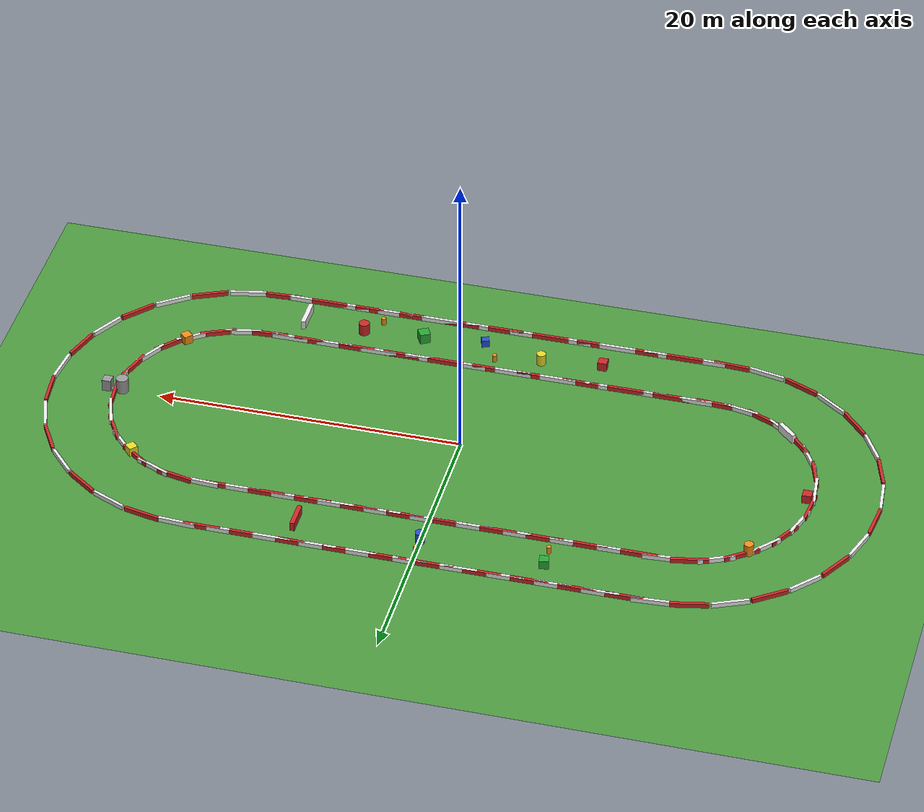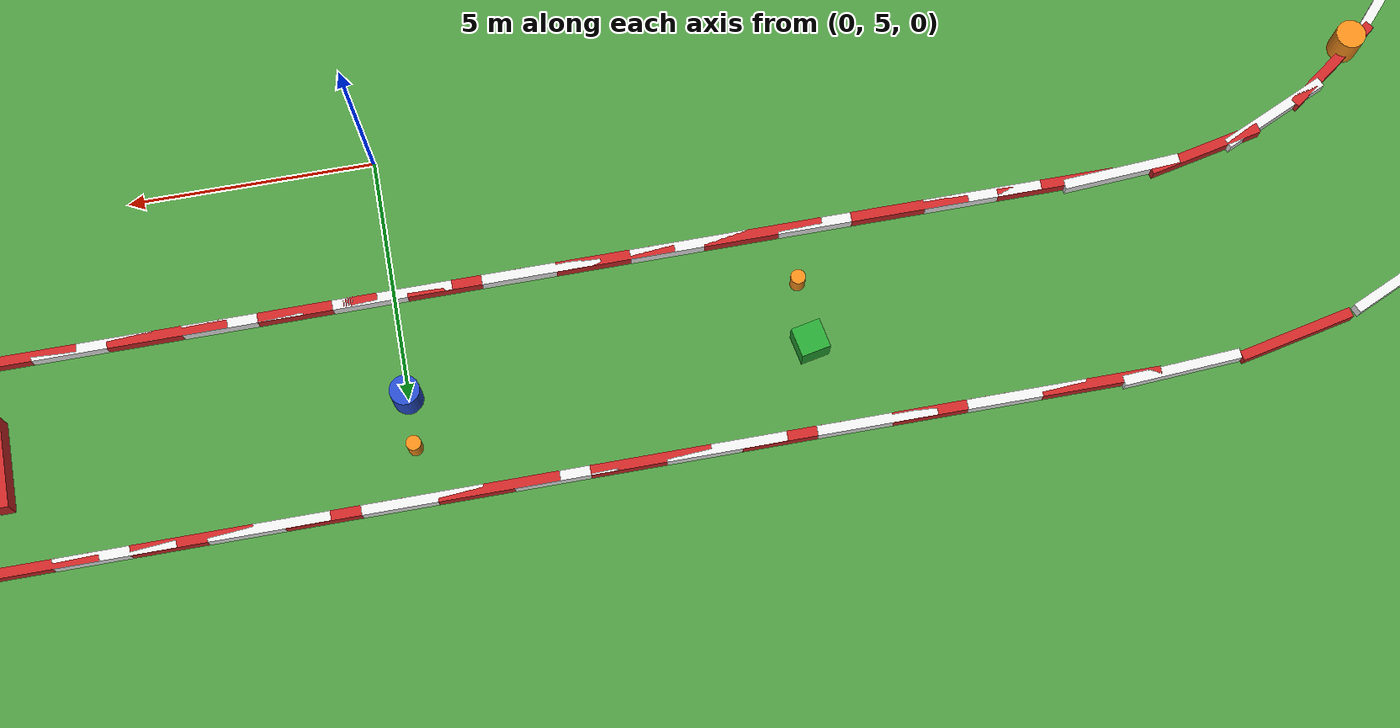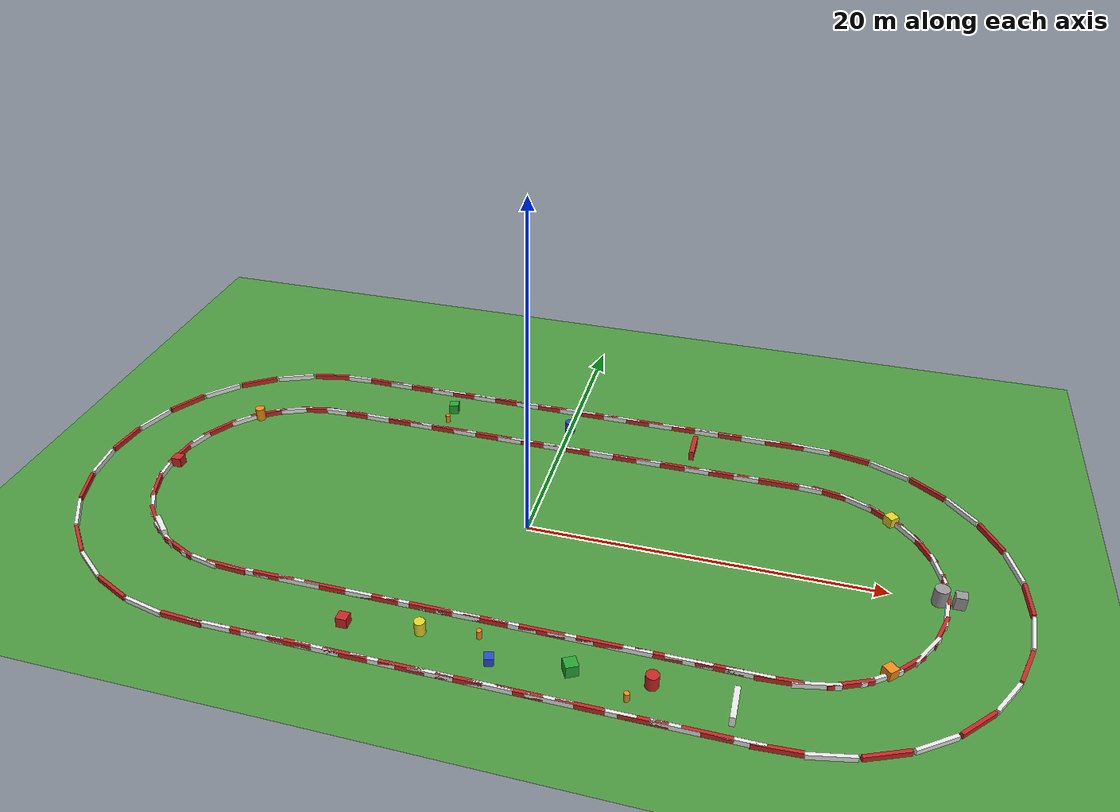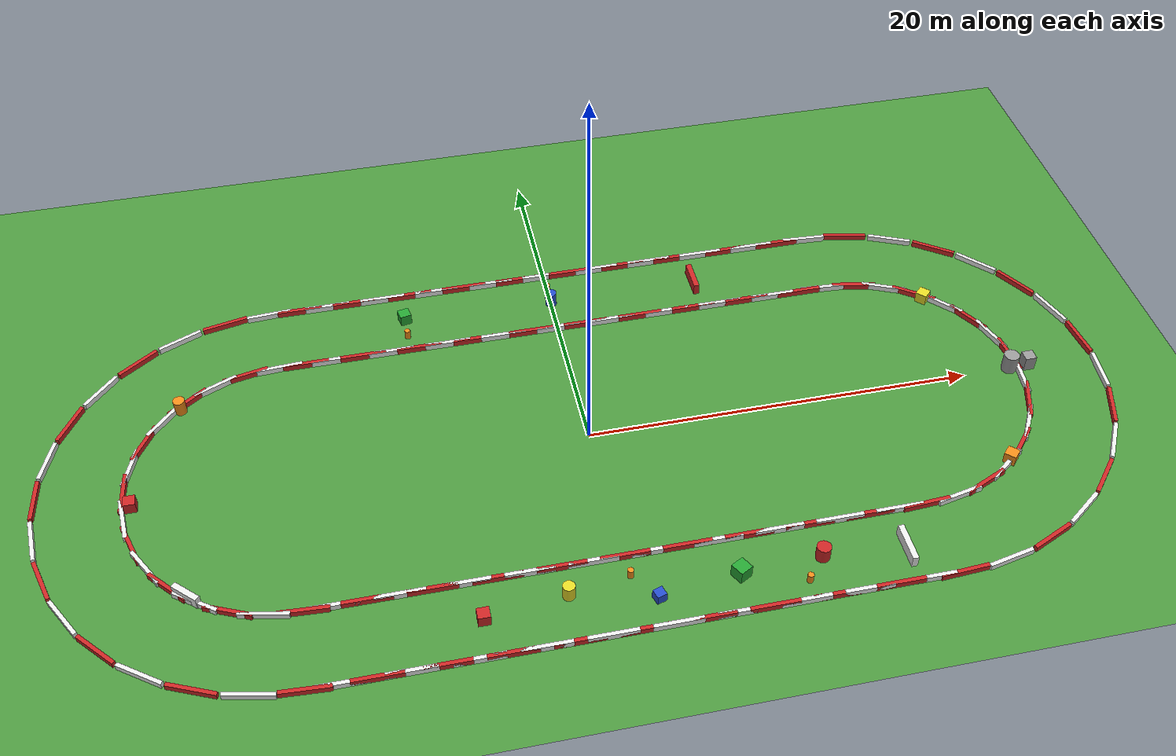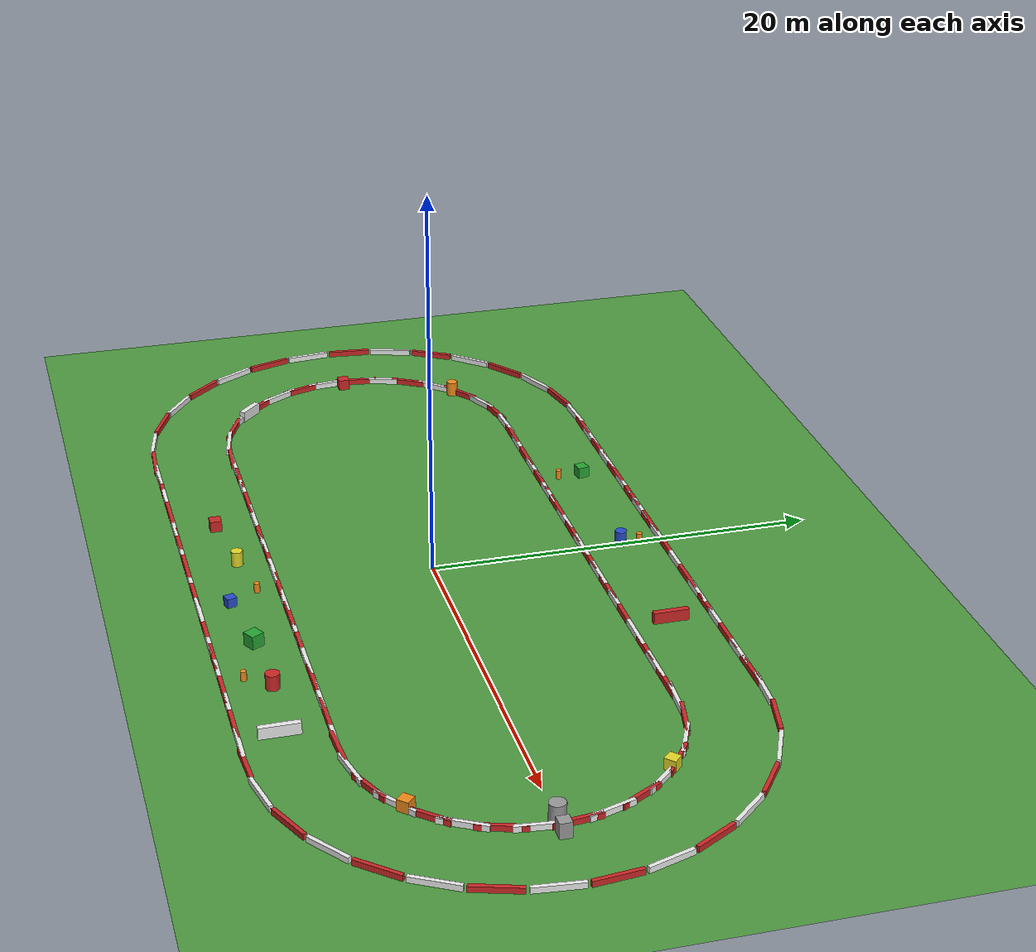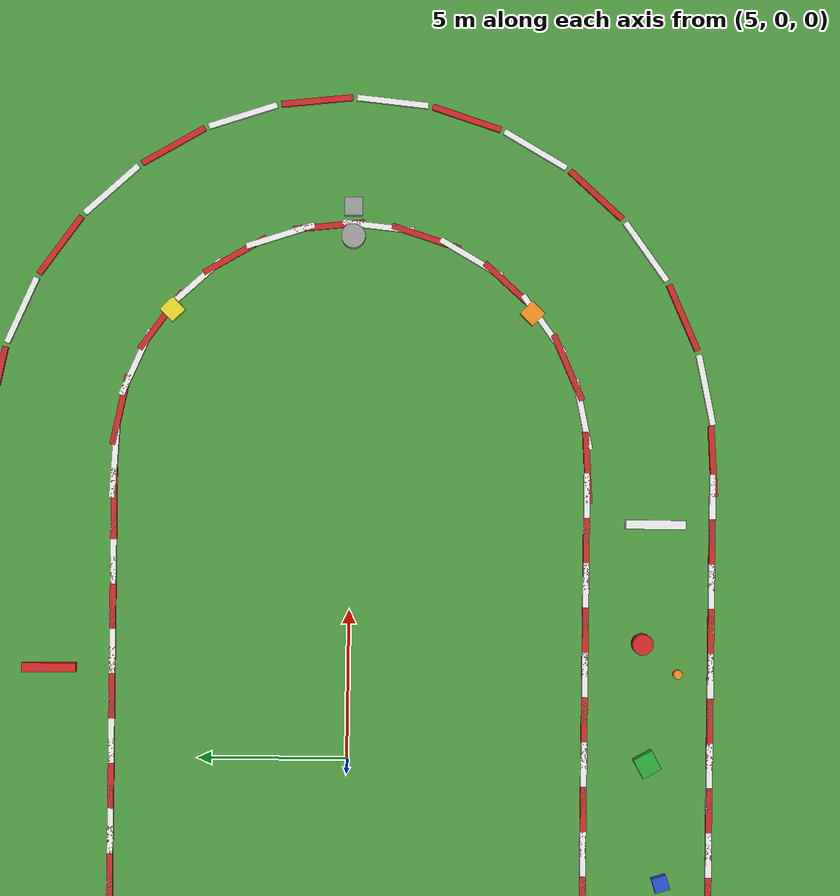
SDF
<sdf version="1.6">
 <world name="road_world">
  <scene>
   <sky>
    <time>16.0</time>
    <clouds>
     <speed>8.0</speed>
     <humidity>0.7</humidity>
     <mean_size>0.5</mean_size>
     <ambient>0.7 0.7 0.7 1.0</ambient>
    </clouds>
   </sky>
   <fog>
    <color>0.7 0.75 0.8 1.0</color>
    <type>linear</type>
    <start>2.0</start>
    <end>25.0</end>
    <density>0.08</density>
   </fog>
   <ambient>0.6 0.6 0.6 1.0</ambient>
   <background>0.7 0.75 0.8 1.0</background>
   <shadows>true</shadows>
  </scene>
  <include><uri>model://sun</uri></include>
  <model name="grass_ground_plane">
   <static>true</static>
   <link name="link">
    <collision name="collision">
     <geometry><plane><normal>0 0 1</normal><size>150 150</size></plane></geometry>
     <surface>
      <contact><collide_bitmask>0xffff</collide_bitmask></contact>
      <friction><ode><mu>100</mu><mu2>50</mu2></ode></friction>
     </surface>
    </collision>
    <visual name="visual">
     <cast_shadows>false</cast_shadows>
     <geometry><plane><normal>0 0 1</normal><size>150 150</size></plane></geometry>
     <material>
      <script><uri>file://media/materials/scripts/gazebo.material</uri><name>Gazebo/Grass</name></script>
     </material>
    </visual>
   </link>
  </model>
  <model name="left_curb_0">
   <static>true</static>
   <pose>-14.872 -7.904 0.15 0 0 -0.061</pose>
   <link name="link">
    <collision name="collision"><geometry><box><size>2.4 0.2 0.3</size></box></geometry></collision>
    <visual name="visual">
     <geometry><box><size>2.4 0.2 0.3</size></box></geometry>
     <material>
      <script><uri>file://media/materials/scripts/gazebo.material</uri><name>Gazebo/Red</name></script>
     </material>
    </visual>
   </link>
  </model>
  <model name="left_curb_1">
   <static>true</static>
   <pose>-13.500 -7.900 0.15 0 0 0.000</pose>
   <link name="link">
    <collision name="collision"><geometry><box><size>2.4 0.2 0.3</size></box></geometry></collision>
    <visual name="visual">
     <geometry><box><size>2.4 0.2 0.3</size></box></geometry>
     <material>
      <script><uri>file://media/materials/scripts/gazebo.material</uri><name>Gazebo/White</name></script>
     </material>
    </visual>
   </link>
  </model>
  <model name="left_curb_2">
   <static>true</static>
   <pose>-12.000 -7.900 0.15 0 0 0.000</pose>
   <link name="link">
    <collision name="collision"><geometry><box><size>2.4 0.2 0.3</size></box></geometry></collision>
    <visual name="visual">
     <geometry><box><size>2.4 0.2 0.3</size></box></geometry>
     <material>
      <script><uri>file://media/materials/scripts/gazebo.material</uri><name>Gazebo/Red</name></script>
     </material>
    </visual>
   </link>
  </model>
  <model name="left_curb_3">
   <static>true</static>
   <pose>-10.500 -7.900 0.15 0 0 0.000</pose>
   <link name="link">
    <collision name="collision"><geometry><box><size>2.4 0.2 0.3</size></box></geometry></collision>
    <visual name="visual">
     <geometry><box><size>2.4 0.2 0.3</size></box></geometry>
     <material>
      <script><uri>file://media/materials/scripts/gazebo.material</uri><name>Gazebo/White</name></script>
     </material>
    </visual>
   </link>
  </model>
  <model name="left_curb_4">
   <static>true</static>
   <pose>-9.000 -7.900 0.15 0 0 0.000</pose>
   <link name="link">
    <collision name="collision"><geometry><box><size>2.4 0.2 0.3</size></box></geometry></collision>
    <visual name="visual">
     <geometry><box><size>2.4 0.2 0.3</size></box></geometry>
     <material>
      <script><uri>file://media/materials/scripts/gazebo.material</uri><name>Gazebo/Red</name></script>
     </material>
    </visual>
   </link>
  </model>
  <model name="left_curb_5">
   <static>true</static>
   <pose>-7.500 -7.900 0.15 0 0 0.000</pose>
   <link name="link">
    <collision name="collision"><geometry><box><size>2.4 0.2 0.3</size></box></geometry></collision>
    <visual name="visual">
     <geometry><box><size>2.4 0.2 0.3</size></box></geometry>
     <material>
      <script><uri>file://media/materials/scripts/gazebo.material</uri><name>Gazebo/White</name></script>
     </material>
    </visual>
   </link>
  </model>
  <model name="left_curb_6">
   <static>true</static>
   <pose>-6.000 -7.900 0.15 0 0 0.000</pose>
   <link name="link">
    <collision name="collision"><geometry><box><size>2.4 0.2 0.3</size></box></geometry></collision>
    <visual name="visual">
     <geometry><box><size>2.4 0.2 0.3</size></box></geometry>
     <material>
      <script><uri>file://media/materials/scripts/gazebo.material</uri><name>Gazebo/Red</name></script>
     </material>
    </visual>
   </link>
  </model>
  <model name="left_curb_7">
   <static>true</static>
   <pose>-4.500 -7.900 0.15 0 0 0.000</pose>
   <link name="link">
    <collision name="collision"><geometry><box><size>2.4 0.2 0.3</size></box></geometry></collision>
    <visual name="visual">
     <geometry><box><size>2.4 0.2 0.3</size></box></geometry>
     <material>
      <script><uri>file://media/materials/scripts/gazebo.material</uri><name>Gazebo/White</name></script>
     </material>
    </visual>
   </link>
  </model>
  <model name="left_curb_8">
   <static>true</static>
   <pose>-3.000 -7.900 0.15 0 0 0.000</pose>
   <link name="link">
    <collision name="collision"><geometry><box><size>2.4 0.2 0.3</size></box></geometry></collision>
    <visual name="visual">
     <geometry><box><size>2.4 0.2 0.3</size></box></geometry>
     <material>
      <script><uri>file://media/materials/scripts/gazebo.material</uri><name>Gazebo/Red</name></script>
     </material>
    </visual>
   </link>
  </model>
  <model name="left_curb_9">
   <static>true</static>
   <pose>-1.500 -7.900 0.15 0 0 0.000</pose>
   <link name="link">
    <collision name="collision"><geometry><box><size>2.4 0.2 0.3</size></box></geometry></collision>
    <visual name="visual">
     <geometry><box><size>2.4 0.2 0.3</size></box></geometry>
     <material>
      <script><uri>file://media/materials/scripts/gazebo.material</uri><name>Gazebo/White</name></script>
     </material>
    </visual>
   </link>
  </model>
  <model name="left_curb_10">
   <static>true</static>
   <pose>0.000 -7.900 0.15 0 0 0.000</pose>
   <link name="link">
    <collision name="collision"><geometry><box><size>2.4 0.2 0.3</size></box></geometry></collision>
    <visual name="visual">
     <geometry><box><size>2.4 0.2 0.3</size></box></geometry>
     <material>
      <script><uri>file://media/materials/scripts/gazebo.material</uri><name>Gazebo/Red</name></script>
     </material>
    </visual>
   </link>
  </model>
  <model name="left_curb_11">
   <static>true</static>
   <pose>1.500 -7.900 0.15 0 0 0.000</pose>
   <link name="link">
    <collision name="collision"><geometry><box><size>2.4 0.2 0.3</size></box></geometry></collision>
    <visual name="visual">
     <geometry><box><size>2.4 0.2 0.3</size></box></geometry>
     <material>
      <script><uri>file://media/materials/scripts/gazebo.material</uri><name>Gazebo/White</name></script>
     </material>
    </visual>
   </link>
  </model>
  <model name="left_curb_12">
   <static>true</static>
   <pose>3.000 -7.900 0.15 0 0 0.000</pose>
   <link name="link">
    <collision name="collision"><geometry><box><size>2.4 0.2 0.3</size></box></geometry></collision>
    <visual name="visual">
     <geometry><box><size>2.4 0.2 0.3</size></box></geometry>
     <material>
      <script><uri>file://media/materials/scripts/gazebo.material</uri><name>Gazebo/Red</name></script>
     </material>
    </visual>
   </link>
  </model>
  <model name="left_curb_13">
   <static>true</static>
   <pose>4.500 -7.900 0.15 0 0 0.000</pose>
   <link name="link">
    <collision name="collision"><geometry><box><size>2.4 0.2 0.3</size></box></geometry></collision>
    <visual name="visual">
     <geometry><box><size>2.4 0.2 0.3</size></box></geometry>
     <material>
      <script><uri>file://media/materials/scripts/gazebo.material</uri><name>Gazebo/White</name></script>
     </material>
    </visual>
   </link>
  </model>
  <model name="left_curb_14">
   <static>true</static>
   <pose>6.000 -7.900 0.15 0 0 0.000</pose>
   <link name="link">
    <collision name="collision"><geometry><box><size>2.4 0.2 0.3</size></box></geometry></collision>
    <visual name="visual">
     <geometry><box><size>2.4 0.2 0.3</size></box></geometry>
     <material>
      <script><uri>file://media/materials/scripts/gazebo.material</uri><name>Gazebo/Red</name></script>
     </material>
    </visual>
   </link>
  </model>
  <model name="left_curb_15">
   <static>true</static>
   <pose>7.500 -7.900 0.15 0 0 0.000</pose>
   <link name="link">
    <collision name="collision"><geometry><box><size>2.4 0.2 0.3</size></box></geometry></collision>
    <visual name="visual">
     <geometry><box><size>2.4 0.2 0.3</size></box></geometry>
     <material>
      <script><uri>file://media/materials/scripts/gazebo.material</uri><name>Gazebo/White</name></script>
     </material>
    </visual>
   </link>
  </model>
  <model name="left_curb_16">
   <static>true</static>
   <pose>9.000 -7.900 0.15 0 0 0.000</pose>
   <link name="link">
    <collision name="collision"><geometry><box><size>2.4 0.2 0.3</size></box></geometry></collision>
    <visual name="visual">
     <geometry><box><size>2.4 0.2 0.3</size></box></geometry>
     <material>
      <script><uri>file://media/materials/scripts/gazebo.material</uri><name>Gazebo/Red</name></script>
     </material>
    </visual>
   </link>
  </model>
  <model name="left_curb_17">
   <static>true</static>
   <pose>10.500 -7.900 0.15 0 0 0.000</pose>
   <link name="link">
    <collision name="collision"><geometry><box><size>2.4 0.2 0.3</size></box></geometry></collision>
    <visual name="visual">
     <geometry><box><size>2.4 0.2 0.3</size></box></geometry>
     <material>
      <script><uri>file://media/materials/scripts/gazebo.material</uri><name>Gazebo/White</name></script>
     </material>
    </visual>
   </link>
  </model>
  <model name="left_curb_18">
   <static>true</static>
   <pose>12.000 -7.900 0.15 0 0 0.000</pose>
   <link name="link">
    <collision name="collision"><geometry><box><size>2.4 0.2 0.3</size></box></geometry></collision>
    <visual name="visual">
     <geometry><box><size>2.4 0.2 0.3</size></box></geometry>
     <material>
      <script><uri>file://media/materials/scripts/gazebo.material</uri><name>Gazebo/Red</name></script>
     </material>
    </visual>
   </link>
  </model>
  <model name="left_curb_19">
   <static>true</static>
   <pose>13.500 -7.900 0.15 0 0 0.000</pose>
   <link name="link">
    <collision name="collision"><geometry><box><size>2.4 0.2 0.3</size></box></geometry></collision>
    <visual name="visual">
     <geometry><box><size>2.4 0.2 0.3</size></box></geometry>
     <material>
      <script><uri>file://media/materials/scripts/gazebo.material</uri><name>Gazebo/White</name></script>
     </material>
    </visual>
   </link>
  </model>
  <model name="left_curb_20">
   <static>true</static>
   <pose>14.872 -7.904 0.15 0 0 0.061</pose>
   <link name="link">
    <collision name="collision"><geometry><box><size>2.4 0.2 0.3</size></box></geometry></collision>
    <visual name="visual">
     <geometry><box><size>2.4 0.2 0.3</size></box></geometry>
     <material>
      <script><uri>file://media/materials/scripts/gazebo.material</uri><name>Gazebo/Red</name></script>
     </material>
    </visual>
   </link>
  </model>
  <model name="left_curb_21">
   <static>true</static>
   <pose>16.643 -7.727 0.15 0 0 0.209</pose>
   <link name="link">
    <collision name="collision"><geometry><box><size>2.4 0.2 0.3</size></box></geometry></collision>
    <visual name="visual">
     <geometry><box><size>2.4 0.2 0.3</size></box></geometry>
     <material>
      <script><uri>file://media/materials/scripts/gazebo.material</uri><name>Gazebo/White</name></script>
     </material>
    </visual>
   </link>
  </model>
  <model name="left_curb_22">
   <static>true</static>
   <pose>18.213 -7.217 0.15 0 0 0.419</pose>
   <link name="link">
    <collision name="collision"><geometry><box><size>2.4 0.2 0.3</size></box></geometry></collision>
    <visual name="visual">
     <geometry><box><size>2.4 0.2 0.3</size></box></geometry>
     <material>
      <script><uri>file://media/materials/scripts/gazebo.material</uri><name>Gazebo/Red</name></script>
     </material>
    </visual>
   </link>
  </model>
  <model name="left_curb_23">
   <static>true</static>
   <pose>19.644 -6.391 0.15 0 0 0.628</pose>
   <link name="link">
    <collision name="collision"><geometry><box><size>2.4 0.2 0.3</size></box></geometry></collision>
    <visual name="visual">
     <geometry><box><size>2.4 0.2 0.3</size></box></geometry>
     <material>
      <script><uri>file://media/materials/scripts/gazebo.material</uri><name>Gazebo/White</name></script>
     </material>
    </visual>
   </link>
  </model>
  <model name="left_curb_24">
   <static>true</static>
   <pose>20.871 -5.286 0.15 0 0 0.838</pose>
   <link name="link">
    <collision name="collision"><geometry><box><size>2.4 0.2 0.3</size></box></geometry></collision>
    <visual name="visual">
     <geometry><box><size>2.4 0.2 0.3</size></box></geometry>
     <material>
      <script><uri>file://media/materials/scripts/gazebo.material</uri><name>Gazebo/Red</name></script>
     </material>
    </visual>
   </link>
  </model>
  <model name="left_curb_25">
   <static>true</static>
   <pose>21.842 -3.950 0.15 0 0 1.047</pose>
   <link name="link">
    <collision name="collision"><geometry><box><size>2.4 0.2 0.3</size></box></geometry></collision>
    <visual name="visual">
     <geometry><box><size>2.4 0.2 0.3</size></box></geometry>
     <material>
      <script><uri>file://media/materials/scripts/gazebo.material</uri><name>Gazebo/White</name></script>
     </material>
    </visual>
   </link>
  </model>
  <model name="left_curb_26">
   <static>true</static>
   <pose>22.513 -2.441 0.15 0 0 1.257</pose>
   <link name="link">
    <collision name="collision"><geometry><box><size>2.4 0.2 0.3</size></box></geometry></collision>
    <visual name="visual">
     <geometry><box><size>2.4 0.2 0.3</size></box></geometry>
     <material>
      <script><uri>file://media/materials/scripts/gazebo.material</uri><name>Gazebo/Red</name></script>
     </material>
    </visual>
   </link>
  </model>
  <model name="left_curb_27">
   <static>true</static>
   <pose>22.857 -0.826 0.15 0 0 1.466</pose>
   <link name="link">
    <collision name="collision"><geometry><box><size>2.4 0.2 0.3</size></box></geometry></collision>
    <visual name="visual">
     <geometry><box><size>2.4 0.2 0.3</size></box></geometry>
     <material>
      <script><uri>file://media/materials/scripts/gazebo.material</uri><name>Gazebo/White</name></script>
     </material>
    </visual>
   </link>
  </model>
  <model name="left_curb_28">
   <static>true</static>
   <pose>22.857 0.826 0.15 0 0 1.676</pose>
   <link name="link">
    <collision name="collision"><geometry><box><size>2.4 0.2 0.3</size></box></geometry></collision>
    <visual name="visual">
     <geometry><box><size>2.4 0.2 0.3</size></box></geometry>
     <material>
      <script><uri>file://media/materials/scripts/gazebo.material</uri><name>Gazebo/Red</name></script>
     </material>
    </visual>
   </link>
  </model>
  <model name="left_curb_29">
   <static>true</static>
   <pose>22.513 2.441 0.15 0 0 1.885</pose>
   <link name="link">
    <collision name="collision"><geometry><box><size>2.4 0.2 0.3</size></box></geometry></collision>
    <visual name="visual">
     <geometry><box><size>2.4 0.2 0.3</size></box></geometry>
     <material>
      <script><uri>file://media/materials/scripts/gazebo.material</uri><name>Gazebo/White</name></script>
     </material>
    </visual>
   </link>
  </model>
  <model name="left_curb_30">
   <static>true</static>
   <pose>21.842 3.950 0.15 0 0 2.094</pose>
   <link name="link">
    <collision name="collision"><geometry><box><size>2.4 0.2 0.3</size></box></geometry></collision>
    <visual name="visual">
     <geometry><box><size>2.4 0.2 0.3</size></box></geometry>
     <material>
      <script><uri>file://media/materials/scripts/gazebo.material</uri><name>Gazebo/Red</name></script>
     </material>
    </visual>
   </link>
  </model>
  <model name="left_curb_31">
   <static>true</static>
   <pose>20.871 5.286 0.15 0 0 2.304</pose>
   <link name="link">
    <collision name="collision"><geometry><box><size>2.4 0.2 0.3</size></box></geometry></collision>
    <visual name="visual">
     <geometry><box><size>2.4 0.2 0.3</size></box></geometry>
     <material>
      <script><uri>file://media/materials/scripts/gazebo.material</uri><name>Gazebo/White</name></script>
     </material>
    </visual>
   </link>
  </model>
  <model name="left_curb_32">
   <static>true</static>
   <pose>19.644 6.391 0.15 0 0 2.513</pose>
   <link name="link">
    <collision name="collision"><geometry><box><size>2.4 0.2 0.3</size></box></geometry></collision>
    <visual name="visual">
     <geometry><box><size>2.4 0.2 0.3</size></box></geometry>
     <material>
      <script><uri>file://media/materials/scripts/gazebo.material</uri><name>Gazebo/Red</name></script>
     </material>
    </visual>
   </link>
  </model>
  <model name="left_curb_33">
   <static>true</static>
   <pose>18.213 7.217 0.15 0 0 2.723</pose>
   <link name="link">
    <collision name="collision"><geometry><box><size>2.4 0.2 0.3</size></box></geometry></collision>
    <visual name="visual">
     <geometry><box><size>2.4 0.2 0.3</size></box></geometry>
     <material>
      <script><uri>file://media/materials/scripts/gazebo.material</uri><name>Gazebo/White</name></script>
     </material>
    </visual>
   </link>
  </model>
  <model name="left_curb_34">
   <static>true</static>
   <pose>16.643 7.727 0.15 0 0 2.932</pose>
   <link name="link">
    <collision name="collision"><geometry><box><size>2.4 0.2 0.3</size></box></geometry></collision>
    <visual name="visual">
     <geometry><box><size>2.4 0.2 0.3</size></box></geometry>
     <material>
      <script><uri>file://media/materials/scripts/gazebo.material</uri><name>Gazebo/Red</name></script>
     </material>
    </visual>
   </link>
  </model>
  <model name="left_curb_35">
   <static>true</static>
   <pose>14.872 7.904 0.15 0 0 3.081</pose>
   <link name="link">
    <collision name="collision"><geometry><box><size>2.4 0.2 0.3</size></box></geometry></collision>
    <visual name="visual">
     <geometry><box><size>2.4 0.2 0.3</size></box></geometry>
     <material>
      <script><uri>file://media/materials/scripts/gazebo.material</uri><name>Gazebo/White</name></script>
     </material>
    </visual>
   </link>
  </model>
  <model name="left_curb_36">
   <static>true</static>
   <pose>13.500 7.900 0.15 0 0 3.142</pose>
   <link name="link">
    <collision name="collision"><geometry><box><size>2.4 0.2 0.3</size></box></geometry></collision>
    <visual name="visual">
     <geometry><box><size>2.4 0.2 0.3</size></box></geometry>
     <material>
      <script><uri>file://media/materials/scripts/gazebo.material</uri><name>Gazebo/Red</name></script>
     </material>
    </visual>
   </link>
  </model>
  <model name="left_curb_37">
   <static>true</static>
   <pose>12.000 7.900 0.15 0 0 3.142</pose>
   <link name="link">
    <collision name="collision"><geometry><box><size>2.4 0.2 0.3</size></box></geometry></collision>
    <visual name="visual">
     <geometry><box><size>2.4 0.2 0.3</size></box></geometry>
     <material>
      <script><uri>file://media/materials/scripts/gazebo.material</uri><name>Gazebo/White</name></script>
     </material>
    </visual>
   </link>
  </model>
  <model name="left_curb_38">
   <static>true</static>
   <pose>10.500 7.900 0.15 0 0 3.142</pose>
   <link name="link">
    <collision name="collision"><geometry><box><size>2.4 0.2 0.3</size></box></geometry></collision>
    <visual name="visual">
     <geometry><box><size>2.4 0.2 0.3</size></box></geometry>
     <material>
      <script><uri>file://media/materials/scripts/gazebo.material</uri><name>Gazebo/Red</name></script>
     </material>
    </visual>
   </link>
  </model>
  <model name="left_curb_39">
   <static>true</static>
   <pose>9.000 7.900 0.15 0 0 3.142</pose>
   <link name="link">
    <collision name="collision"><geometry><box><size>2.4 0.2 0.3</size></box></geometry></collision>
    <visual name="visual">
     <geometry><box><size>2.4 0.2 0.3</size></box></geometry>
     <material>
      <script><uri>file://media/materials/scripts/gazebo.material</uri><name>Gazebo/White</name></script>
     </material>
    </visual>
   </link>
  </model>
  <model name="left_curb_40">
   <static>true</static>
   <pose>7.500 7.900 0.15 0 0 3.142</pose>
   <link name="link">
    <collision name="collision"><geometry><box><size>2.4 0.2 0.3</size></box></geometry></collision>
    <visual name="visual">
     <geometry><box><size>2.4 0.2 0.3</size></box></geometry>
     <material>
      <script><uri>file://media/materials/scripts/gazebo.material</uri><name>Gazebo/Red</name></script>
     </material>
    </visual>
   </link>
  </model>
  <model name="left_curb_41">
   <static>true</static>
   <pose>6.000 7.900 0.15 0 0 3.142</pose>
   <link name="link">
    <collision name="collision"><geometry><box><size>2.4 0.2 0.3</size></box></geometry></collision>
    <visual name="visual">
     <geometry><box><size>2.4 0.2 0.3</size></box></geometry>
     <material>
      <script><uri>file://media/materials/scripts/gazebo.material</uri><name>Gazebo/White</name></script>
     </material>
    </visual>
   </link>
  </model>
  <model name="left_curb_42">
   <static>true</static>
   <pose>4.500 7.900 0.15 0 0 3.142</pose>
   <link name="link">
    <collision name="collision"><geometry><box><size>2.4 0.2 0.3</size></box></geometry></collision>
    <visual name="visual">
     <geometry><box><size>2.4 0.2 0.3</size></box></geometry>
     <material>
      <script><uri>file://media/materials/scripts/gazebo.material</uri><name>Gazebo/Red</name></script>
     </material>
    </visual>
   </link>
  </model>
  <model name="left_curb_43">
   <static>true</static>
   <pose>3.000 7.900 0.15 0 0 3.142</pose>
   <link name="link">
    <collision name="collision"><geometry><box><size>2.4 0.2 0.3</size></box></geometry></collision>
    <visual name="visual">
     <geometry><box><size>2.4 0.2 0.3</size></box></geometry>
     <material>
      <script><uri>file://media/materials/scripts/gazebo.material</uri><name>Gazebo/White</name></script>
     </material>
    </visual>
   </link>
  </model>
  <model name="left_curb_44">
   <static>true</static>
   <pose>1.500 7.900 0.15 0 0 3.142</pose>
   <link name="link">
    <collision name="collision"><geometry><box><size>2.4 0.2 0.3</size></box></geometry></collision>
    <visual name="visual">
     <geometry><box><size>2.4 0.2 0.3</size></box></geometry>
     <material>
      <script><uri>file://media/materials/scripts/gazebo.material</uri><name>Gazebo/Red</name></script>
     </material>
    </visual>
   </link>
  </model>
  <model name="left_curb_45">
   <static>true</static>
   <pose>0.000 7.900 0.15 0 0 3.142</pose>
   <link name="link">
    <collision name="collision"><geometry><box><size>2.4 0.2 0.3</size></box></geometry></collision>
    <visual name="visual">
     <geometry><box><size>2.4 0.2 0.3</size></box></geometry>
     <material>
      <script><uri>file://media/materials/scripts/gazebo.material</uri><name>Gazebo/White</name></script>
     </material>
    </visual>
   </link>
  </model>
  <model name="left_curb_46">
   <static>true</static>
   <pose>-1.500 7.900 0.15 0 0 3.142</pose>
   <link name="link">
    <collision name="collision"><geometry><box><size>2.4 0.2 0.3</size></box></geometry></collision>
    <visual name="visual">
     <geometry><box><size>2.4 0.2 0.3</size></box></geometry>
     <material>
      <script><uri>file://media/materials/scripts/gazebo.material</uri><name>Gazebo/Red</name></script>
     </material>
    </visual>
   </link>
  </model>
  <model name="left_curb_47">
   <static>true</static>
   <pose>-3.000 7.900 0.15 0 0 3.142</pose>
   <link name="link">
    <collision name="collision"><geometry><box><size>2.4 0.2 0.3</size></box></geometry></collision>
    <visual name="visual">
     <geometry><box><size>2.4 0.2 0.3</size></box></geometry>
     <material>
      <script><uri>file://media/materials/scripts/gazebo.material</uri><name>Gazebo/White</name></script>
     </material>
    </visual>
   </link>
  </model>
  <model name="left_curb_48">
   <static>true</static>
   <pose>-4.500 7.900 0.15 0 0 3.142</pose>
   <link name="link">
    <collision name="collision"><geometry><box><size>2.4 0.2 0.3</size></box></geometry></collision>
    <visual name="visual">
     <geometry><box><size>2.4 0.2 0.3</size></box></geometry>
     <material>
      <script><uri>file://media/materials/scripts/gazebo.material</uri><name>Gazebo/Red</name></script>
     </material>
    </visual>
   </link>
  </model>
  <model name="left_curb_49">
   <static>true</static>
   <pose>-6.000 7.900 0.15 0 0 3.142</pose>
   <link name="link">
    <collision name="collision"><geometry><box><size>2.4 0.2 0.3</size></box></geometry></collision>
    <visual name="visual">
     <geometry><box><size>2.4 0.2 0.3</size></box></geometry>
     <material>
      <script><uri>file://media/materials/scripts/gazebo.material</uri><name>Gazebo/White</name></script>
     </material>
    </visual>
   </link>
  </model>
  <model name="left_curb_50">
   <static>true</static>
   <pose>-7.500 7.900 0.15 0 0 3.142</pose>
   <link name="link">
    <collision name="collision"><geometry><box><size>2.4 0.2 0.3</size></box></geometry></collision>
    <visual name="visual">
     <geometry><box><size>2.4 0.2 0.3</size></box></geometry>
     <material>
      <script><uri>file://media/materials/scripts/gazebo.material</uri><name>Gazebo/Red</name></script>
     </material>
    </visual>
   </link>
  </model>
  <model name="left_curb_51">
   <static>true</static>
   <pose>-9.000 7.900 0.15 0 0 3.142</pose>
   <link name="link">
    <collision name="collision"><geometry><box><size>2.4 0.2 0.3</size></box></geometry></collision>
    <visual name="visual">
     <geometry><box><size>2.4 0.2 0.3</size></box></geometry>
     <material>
      <script><uri>file://media/materials/scripts/gazebo.material</uri><name>Gazebo/White</name></script>
     </material>
    </visual>
   </link>
  </model>
  <model name="left_curb_52">
   <static>true</static>
   <pose>-10.500 7.900 0.15 0 0 3.142</pose>
   <link name="link">
    <collision name="collision"><geometry><box><size>2.4 0.2 0.3</size></box></geometry></collision>
    <visual name="visual">
     <geometry><box><size>2.4 0.2 0.3</size></box></geometry>
     <material>
      <script><uri>file://media/materials/scripts/gazebo.material</uri><name>Gazebo/Red</name></script>
     </material>
    </visual>
   </link>
  </model>
  <model name="left_curb_53">
   <static>true</static>
   <pose>-12.000 7.900 0.15 0 0 3.142</pose>
   <link name="link">
    <collision name="collision"><geometry><box><size>2.4 0.2 0.3</size></box></geometry></collision>
    <visual name="visual">
     <geometry><box><size>2.4 0.2 0.3</size></box></geometry>
     <material>
      <script><uri>file://media/materials/scripts/gazebo.material</uri><name>Gazebo/White</name></script>
     </material>
    </visual>
   </link>
  </model>
  <model name="left_curb_54">
   <static>true</static>
   <pose>-13.500 7.900 0.15 0 0 3.142</pose>
   <link name="link">
    <collision name="collision"><geometry><box><size>2.4 0.2 0.3</size></box></geometry></collision>
    <visual name="visual">
     <geometry><box><size>2.4 0.2 0.3</size></box></geometry>
     <material>
      <script><uri>file://media/materials/scripts/gazebo.material</uri><name>Gazebo/Red</name></script>
     </material>
    </visual>
   </link>
  </model>
  <model name="left_curb_55">
   <static>true</static>
   <pose>-14.872 7.904 0.15 0 0 -3.081</pose>
   <link name="link">
    <collision name="collision"><geometry><box><size>2.4 0.2 0.3</size></box></geometry></collision>
    <visual name="visual">
     <geometry><box><size>2.4 0.2 0.3</size></box></geometry>
     <material>
      <script><uri>file://media/materials/scripts/gazebo.material</uri><name>Gazebo/White</name></script>
     </material>
    </visual>
   </link>
  </model>
  <model name="left_curb_56">
   <static>true</static>
   <pose>-16.643 7.727 0.15 0 0 -2.932</pose>
   <link name="link">
    <collision name="collision"><geometry><box><size>2.4 0.2 0.3</size></box></geometry></collision>
    <visual name="visual">
     <geometry><box><size>2.4 0.2 0.3</size></box></geometry>
     <material>
      <script><uri>file://media/materials/scripts/gazebo.material</uri><name>Gazebo/Red</name></script>
     </material>
    </visual>
   </link>
  </model>
  <model name="left_curb_57">
   <static>true</static>
   <pose>-18.213 7.217 0.15 0 0 -2.723</pose>
   <link name="link">
    <collision name="collision"><geometry><box><size>2.4 0.2 0.3</size></box></geometry></collision>
    <visual name="visual">
     <geometry><box><size>2.4 0.2 0.3</size></box></geometry>
     <material>
      <script><uri>file://media/materials/scripts/gazebo.material</uri><name>Gazebo/White</name></script>
     </material>
    </visual>
   </link>
  </model>
  <model name="left_curb_58">
   <static>true</static>
   <pose>-19.644 6.391 0.15 0 0 -2.513</pose>
   <link name="link">
    <collision name="collision"><geometry><box><size>2.4 0.2 0.3</size></box></geometry></collision>
    <visual name="visual">
     <geometry><box><size>2.4 0.2 0.3</size></box></geometry>
     <material>
      <script><uri>file://media/materials/scripts/gazebo.material</uri><name>Gazebo/Red</name></script>
     </material>
    </visual>
   </link>
  </model>
  <model name="left_curb_59">
   <static>true</static>
   <pose>-20.871 5.286 0.15 0 0 -2.304</pose>
   <link name="link">
    <collision name="collision"><geometry><box><size>2.4 0.2 0.3</size></box></geometry></collision>
    <visual name="visual">
     <geometry><box><size>2.4 0.2 0.3</size></box></geometry>
     <material>
      <script><uri>file://media/materials/scripts/gazebo.material</uri><name>Gazebo/White</name></script>
     </material>
    </visual>
   </link>
  </model>
  <model name="left_curb_60">
   <static>true</static>
   <pose>-21.842 3.950 0.15 0 0 -2.094</pose>
   <link name="link">
    <collision name="collision"><geometry><box><size>2.4 0.2 0.3</size></box></geometry></collision>
    <visual name="visual">
     <geometry><box><size>2.4 0.2 0.3</size></box></geometry>
     <material>
      <script><uri>file://media/materials/scripts/gazebo.material</uri><name>Gazebo/Red</name></script>
     </material>
    </visual>
   </link>
  </model>
  <model name="left_curb_61">
   <static>true</static>
   <pose>-22.513 2.441 0.15 0 0 -1.885</pose>
   <link name="link">
    <collision name="collision"><geometry><box><size>2.4 0.2 0.3</size></box></geometry></collision>
    <visual name="visual">
     <geometry><box><size>2.4 0.2 0.3</size></box></geometry>
     <material>
      <script><uri>file://media/materials/scripts/gazebo.material</uri><name>Gazebo/White</name></script>
     </material>
    </visual>
   </link>
  </model>
  <model name="left_curb_62">
   <static>true</static>
   <pose>-22.857 0.826 0.15 0 0 -1.676</pose>
   <link name="link">
    <collision name="collision"><geometry><box><size>2.4 0.2 0.3</size></box></geometry></collision>
    <visual name="visual">
     <geometry><box><size>2.4 0.2 0.3</size></box></geometry>
     <material>
      <script><uri>file://media/materials/scripts/gazebo.material</uri><name>Gazebo/Red</name></script>
     </material>
    </visual>
   </link>
  </model>
  <model name="left_curb_63">
   <static>true</static>
   <pose>-22.857 -0.826 0.15 0 0 -1.466</pose>
   <link name="link">
    <collision name="collision"><geometry><box><size>2.4 0.2 0.3</size></box></geometry></collision>
    <visual name="visual">
     <geometry><box><size>2.4 0.2 0.3</size></box></geometry>
     <material>
      <script><uri>file://media/materials/scripts/gazebo.material</uri><name>Gazebo/White</name></script>
     </material>
    </visual>
   </link>
  </model>
  <model name="left_curb_64">
   <static>true</static>
   <pose>-22.513 -2.441 0.15 0 0 -1.257</pose>
   <link name="link">
    <collision name="collision"><geometry><box><size>2.4 0.2 0.3</size></box></geometry></collision>
    <visual name="visual">
     <geometry><box><size>2.4 0.2 0.3</size></box></geometry>
     <material>
      <script><uri>file://media/materials/scripts/gazebo.material</uri><name>Gazebo/Red</name></script>
     </material>
    </visual>
   </link>
  </model>
  <model name="left_curb_65">
   <static>true</static>
   <pose>-21.842 -3.950 0.15 0 0 -1.047</pose>
   <link name="link">
    <collision name="collision"><geometry><box><size>2.4 0.2 0.3</size></box></geometry></collision>
    <visual name="visual">
     <geometry><box><size>2.4 0.2 0.3</size></box></geometry>
     <material>
      <script><uri>file://media/materials/scripts/gazebo.material</uri><name>Gazebo/White</name></script>
     </material>
    </visual>
   </link>
  </model>
  <model name="left_curb_66">
   <static>true</static>
   <pose>-20.871 -5.286 0.15 0 0 -0.838</pose>
   <link name="link">
    <collision name="collision"><geometry><box><size>2.4 0.2 0.3</size></box></geometry></collision>
    <visual name="visual">
     <geometry><box><size>2.4 0.2 0.3</size></box></geometry>
     <material>
      <script><uri>file://media/materials/scripts/gazebo.material</uri><name>Gazebo/Red</name></script>
     </material>
    </visual>
   </link>
  </model>
  <model name="left_curb_67">
   <static>true</static>
   <pose>-19.644 -6.391 0.15 0 0 -0.628</pose>
   <link name="link">
    <collision name="collision"><geometry><box><size>2.4 0.2 0.3</size></box></geometry></collision>
    <visual name="visual">
     <geometry><box><size>2.4 0.2 0.3</size></box></geometry>
     <material>
      <script><uri>file://media/materials/scripts/gazebo.material</uri><name>Gazebo/White</name></script>
     </material>
    </visual>
   </link>
  </model>
  <model name="left_curb_68">
   <static>true</static>
   <pose>-18.213 -7.217 0.15 0 0 -0.419</pose>
   <link name="link">
    <collision name="collision"><geometry><box><size>2.4 0.2 0.3</size></box></geometry></collision>
    <visual name="visual">
     <geometry><box><size>2.4 0.2 0.3</size></box></geometry>
     <material>
      <script><uri>file://media/materials/scripts/gazebo.material</uri><name>Gazebo/Red</name></script>
     </material>
    </visual>
   </link>
  </model>
  <model name="left_curb_69">
   <static>true</static>
   <pose>-16.643 -7.727 0.15 0 0 -0.209</pose>
   <link name="link">
    <collision name="collision"><geometry><box><size>2.4 0.2 0.3</size></box></geometry></collision>
    <visual name="visual">
     <geometry><box><size>2.4 0.2 0.3</size></box></geometry>
     <material>
      <script><uri>file://media/materials/scripts/gazebo.material</uri><name>Gazebo/White</name></script>
     </material>
    </visual>
   </link>
  </model>
  <model name="right_curb_0">
   <static>true</static>
   <pose>-15.128 -12.096 0.15 0 0 -0.061</pose>
   <link name="link">
    <collision name="collision"><geometry><box><size>2.4 0.2 0.3</size></box></geometry></collision>
    <visual name="visual">
     <geometry><box><size>2.4 0.2 0.3</size></box></geometry>
     <material>
      <script><uri>file://media/materials/scripts/gazebo.material</uri><name>Gazebo/Red</name></script>
     </material>
    </visual>
   </link>
  </model>
  <model name="right_curb_1">
   <static>true</static>
   <pose>-13.500 -12.100 0.15 0 0 0.000</pose>
   <link name="link">
    <collision name="collision"><geometry><box><size>2.4 0.2 0.3</size></box></geometry></collision>
    <visual name="visual">
     <geometry><box><size>2.4 0.2 0.3</size></box></geometry>
     <material>
      <script><uri>file://media/materials/scripts/gazebo.material</uri><name>Gazebo/White</name></script>
     </material>
    </visual>
   </link>
  </model>
  <model name="right_curb_2">
   <static>true</static>
   <pose>-12.000 -12.100 0.15 0 0 0.000</pose>
   <link name="link">
    <collision name="collision"><geometry><box><size>2.4 0.2 0.3</size></box></geometry></collision>
    <visual name="visual">
     <geometry><box><size>2.4 0.2 0.3</size></box></geometry>
     <material>
      <script><uri>file://media/materials/scripts/gazebo.material</uri><name>Gazebo/Red</name></script>
     </material>
    </visual>
   </link>
  </model>
  <model name="right_curb_3">
   <static>true</static>
   <pose>-10.500 -12.100 0.15 0 0 0.000</pose>
   <link name="link">
    <collision name="collision"><geometry><box><size>2.4 0.2 0.3</size></box></geometry></collision>
    <visual name="visual">
     <geometry><box><size>2.4 0.2 0.3</size></box></geometry>
     <material>
      <script><uri>file://media/materials/scripts/gazebo.material</uri><name>Gazebo/White</name></script>
     </material>
    </visual>
   </link>
  </model>
  <model name="right_curb_4">
   <static>true</static>
   <pose>-9.000 -12.100 0.15 0 0 0.000</pose>
   <link name="link">
    <collision name="collision"><geometry><box><size>2.4 0.2 0.3</size></box></geometry></collision>
    <visual name="visual">
     <geometry><box><size>2.4 0.2 0.3</size></box></geometry>
     <material>
      <script><uri>file://media/materials/scripts/gazebo.material</uri><name>Gazebo/Red</name></script>
     </material>
    </visual>
   </link>
  </model>
  <model name="right_curb_5">
   <static>true</static>
   <pose>-7.500 -12.100 0.15 0 0 0.000</pose>
   <link name="link">
    <collision name="collision"><geometry><box><size>2.4 0.2 0.3</size></box></geometry></collision>
    <visual name="visual">
     <geometry><box><size>2.4 0.2 0.3</size></box></geometry>
     <material>
      <script><uri>file://media/materials/scripts/gazebo.material</uri><name>Gazebo/White</name></script>
     </material>
    </visual>
   </link>
  </model>
  <model name="right_curb_6">
   <static>true</static>
   <pose>-6.000 -12.100 0.15 0 0 0.000</pose>
   <link name="link">
    <collision name="collision"><geometry><box><size>2.4 0.2 0.3</size></box></geometry></collision>
    <visual name="visual">
     <geometry><box><size>2.4 0.2 0.3</size></box></geometry>
     <material>
      <script><uri>file://media/materials/scripts/gazebo.material</uri><name>Gazebo/Red</name></script>
     </material>
    </visual>
   </link>
  </model>
  <model name="right_curb_7">
   <static>true</static>
   <pose>-4.500 -12.100 0.15 0 0 0.000</pose>
   <link name="link">
    <collision name="collision"><geometry><box><size>2.4 0.2 0.3</size></box></geometry></collision>
    <visual name="visual">
     <geometry><box><size>2.4 0.2 0.3</size></box></geometry>
     <material>
      <script><uri>file://media/materials/scripts/gazebo.material</uri><name>Gazebo/White</name></script>
     </material>
    </visual>
   </link>
  </model>
  <model name="right_curb_8">
   <static>true</static>
   <pose>-3.000 -12.100 0.15 0 0 0.000</pose>
   <link name="link">
    <collision name="collision"><geometry><box><size>2.4 0.2 0.3</size></box></geometry></collision>
    <visual name="visual">
     <geometry><box><size>2.4 0.2 0.3</size></box></geometry>
     <material>
      <script><uri>file://media/materials/scripts/gazebo.material</uri><name>Gazebo/Red</name></script>
     </material>
    </visual>
   </link>
  </model>
  <model name="right_curb_9">
   <static>true</static>
   <pose>-1.500 -12.100 0.15 0 0 0.000</pose>
   <link name="link">
    <collision name="collision"><geometry><box><size>2.4 0.2 0.3</size></box></geometry></collision>
    <visual name="visual">
     <geometry><box><size>2.4 0.2 0.3</size></box></geometry>
     <material>
      <script><uri>file://media/materials/scripts/gazebo.material</uri><name>Gazebo/White</name></script>
     </material>
    </visual>
   </link>
  </model>
  <model name="right_curb_10">
   <static>true</static>
   <pose>0.000 -12.100 0.15 0 0 0.000</pose>
   <link name="link">
    <collision name="collision"><geometry><box><size>2.4 0.2 0.3</size></box></geometry></collision>
    <visual name="visual">
     <geometry><box><size>2.4 0.2 0.3</size></box></geometry>
     <material>
      <script><uri>file://media/materials/scripts/gazebo.material</uri><name>Gazebo/Red</name></script>
     </material>
    </visual>
   </link>
  </model>
  <model name="right_curb_11">
   <static>true</static>
   <pose>1.500 -12.100 0.15 0 0 0.000</pose>
   <link name="link">
    <collision name="collision"><geometry><box><size>2.4 0.2 0.3</size></box></geometry></collision>
    <visual name="visual">
     <geometry><box><size>2.4 0.2 0.3</size></box></geometry>
     <material>
      <script><uri>file://media/materials/scripts/gazebo.material</uri><name>Gazebo/White</name></script>
     </material>
    </visual>
   </link>
  </model>
  <model name="right_curb_12">
   <static>true</static>
   <pose>3.000 -12.100 0.15 0 0 0.000</pose>
   <link name="link">
    <collision name="collision"><geometry><box><size>2.4 0.2 0.3</size></box></geometry></collision>
    <visual name="visual">
     <geometry><box><size>2.4 0.2 0.3</size></box></geometry>
     <material>
      <script><uri>file://media/materials/scripts/gazebo.material</uri><name>Gazebo/Red</name></script>
     </material>
    </visual>
   </link>
  </model>
  <model name="right_curb_13">
   <static>true</static>
   <pose>4.500 -12.100 0.15 0 0 0.000</pose>
   <link name="link">
    <collision name="collision"><geometry><box><size>2.4 0.2 0.3</size></box></geometry></collision>
    <visual name="visual">
     <geometry><box><size>2.4 0.2 0.3</size></box></geometry>
     <material>
      <script><uri>file://media/materials/scripts/gazebo.material</uri><name>Gazebo/White</name></script>
     </material>
    </visual>
   </link>
  </model>
  <model name="right_curb_14">
   <static>true</static>
   <pose>6.000 -12.100 0.15 0 0 0.000</pose>
   <link name="link">
    <collision name="collision"><geometry><box><size>2.4 0.2 0.3</size></box></geometry></collision>
    <visual name="visual">
     <geometry><box><size>2.4 0.2 0.3</size></box></geometry>
     <material>
      <script><uri>file://media/materials/scripts/gazebo.material</uri><name>Gazebo/Red</name></script>
     </material>
    </visual>
   </link>
  </model>
  <model name="right_curb_15">
   <static>true</static>
   <pose>7.500 -12.100 0.15 0 0 0.000</pose>
   <link name="link">
    <collision name="collision"><geometry><box><size>2.4 0.2 0.3</size></box></geometry></collision>
    <visual name="visual">
     <geometry><box><size>2.4 0.2 0.3</size></box></geometry>
     <material>
      <script><uri>file://media/materials/scripts/gazebo.material</uri><name>Gazebo/White</name></script>
     </material>
    </visual>
   </link>
  </model>
  <model name="right_curb_16">
   <static>true</static>
   <pose>9.000 -12.100 0.15 0 0 0.000</pose>
   <link name="link">
    <collision name="collision"><geometry><box><size>2.4 0.2 0.3</size></box></geometry></collision>
    <visual name="visual">
     <geometry><box><size>2.4 0.2 0.3</size></box></geometry>
     <material>
      <script><uri>file://media/materials/scripts/gazebo.material</uri><name>Gazebo/Red</name></script>
     </material>
    </visual>
   </link>
  </model>
  <model name="right_curb_17">
   <static>true</static>
   <pose>10.500 -12.100 0.15 0 0 0.000</pose>
   <link name="link">
    <collision name="collision"><geometry><box><size>2.4 0.2 0.3</size></box></geometry></collision>
    <visual name="visual">
     <geometry><box><size>2.4 0.2 0.3</size></box></geometry>
     <material>
      <script><uri>file://media/materials/scripts/gazebo.material</uri><name>Gazebo/White</name></script>
     </material>
    </visual>
   </link>
  </model>
  <model name="right_curb_18">
   <static>true</static>
   <pose>12.000 -12.100 0.15 0 0 0.000</pose>
   <link name="link">
    <collision name="collision"><geometry><box><size>2.4 0.2 0.3</size></box></geometry></collision>
    <visual name="visual">
     <geometry><box><size>2.4 0.2 0.3</size></box></geometry>
     <material>
      <script><uri>file://media/materials/scripts/gazebo.material</uri><name>Gazebo/Red</name></script>
     </material>
    </visual>
   </link>
  </model>
  <model name="right_curb_19">
   <static>true</static>
   <pose>13.500 -12.100 0.15 0 0 0.000</pose>
   <link name="link">
    <collision name="collision"><geometry><box><size>2.4 0.2 0.3</size></box></geometry></collision>
    <visual name="visual">
     <geometry><box><size>2.4 0.2 0.3</size></box></geometry>
     <material>
      <script><uri>file://media/materials/scripts/gazebo.material</uri><name>Gazebo/White</name></script>
     </material>
    </visual>
   </link>
  </model>
  <model name="right_curb_20">
   <static>true</static>
   <pose>15.128 -12.096 0.15 0 0 0.061</pose>
   <link name="link">
    <collision name="collision"><geometry><box><size>2.4 0.2 0.3</size></box></geometry></collision>
    <visual name="visual">
     <geometry><box><size>2.4 0.2 0.3</size></box></geometry>
     <material>
      <script><uri>file://media/materials/scripts/gazebo.material</uri><name>Gazebo/Red</name></script>
     </material>
    </visual>
   </link>
  </model>
  <model name="right_curb_21">
   <static>true</static>
   <pose>17.516 -11.836 0.15 0 0 0.209</pose>
   <link name="link">
    <collision name="collision"><geometry><box><size>2.4 0.2 0.3</size></box></geometry></collision>
    <visual name="visual">
     <geometry><box><size>2.4 0.2 0.3</size></box></geometry>
     <material>
      <script><uri>file://media/materials/scripts/gazebo.material</uri><name>Gazebo/White</name></script>
     </material>
    </visual>
   </link>
  </model>
  <model name="right_curb_22">
   <static>true</static>
   <pose>19.922 -11.054 0.15 0 0 0.419</pose>
   <link name="link">
    <collision name="collision"><geometry><box><size>2.4 0.2 0.3</size></box></geometry></collision>
    <visual name="visual">
     <geometry><box><size>2.4 0.2 0.3</size></box></geometry>
     <material>
      <script><uri>file://media/materials/scripts/gazebo.material</uri><name>Gazebo/Red</name></script>
     </material>
    </visual>
   </link>
  </model>
  <model name="right_curb_23">
   <static>true</static>
   <pose>22.112 -9.789 0.15 0 0 0.628</pose>
   <link name="link">
    <collision name="collision"><geometry><box><size>2.4 0.2 0.3</size></box></geometry></collision>
    <visual name="visual">
     <geometry><box><size>2.4 0.2 0.3</size></box></geometry>
     <material>
      <script><uri>file://media/materials/scripts/gazebo.material</uri><name>Gazebo/White</name></script>
     </material>
    </visual>
   </link>
  </model>
  <model name="right_curb_24">
   <static>true</static>
   <pose>23.992 -8.096 0.15 0 0 0.838</pose>
   <link name="link">
    <collision name="collision"><geometry><box><size>2.4 0.2 0.3</size></box></geometry></collision>
    <visual name="visual">
     <geometry><box><size>2.4 0.2 0.3</size></box></geometry>
     <material>
      <script><uri>file://media/materials/scripts/gazebo.material</uri><name>Gazebo/Red</name></script>
     </material>
    </visual>
   </link>
  </model>
  <model name="right_curb_25">
   <static>true</static>
   <pose>25.479 -6.050 0.15 0 0 1.047</pose>
   <link name="link">
    <collision name="collision"><geometry><box><size>2.4 0.2 0.3</size></box></geometry></collision>
    <visual name="visual">
     <geometry><box><size>2.4 0.2 0.3</size></box></geometry>
     <material>
      <script><uri>file://media/materials/scripts/gazebo.material</uri><name>Gazebo/White</name></script>
     </material>
    </visual>
   </link>
  </model>
  <model name="right_curb_26">
   <static>true</static>
   <pose>26.508 -3.739 0.15 0 0 1.257</pose>
   <link name="link">
    <collision name="collision"><geometry><box><size>2.4 0.2 0.3</size></box></geometry></collision>
    <visual name="visual">
     <geometry><box><size>2.4 0.2 0.3</size></box></geometry>
     <material>
      <script><uri>file://media/materials/scripts/gazebo.material</uri><name>Gazebo/Red</name></script>
     </material>
    </visual>
   </link>
  </model>
  <model name="right_curb_27">
   <static>true</static>
   <pose>27.034 -1.265 0.15 0 0 1.466</pose>
   <link name="link">
    <collision name="collision"><geometry><box><size>2.4 0.2 0.3</size></box></geometry></collision>
    <visual name="visual">
     <geometry><box><size>2.4 0.2 0.3</size></box></geometry>
     <material>
      <script><uri>file://media/materials/scripts/gazebo.material</uri><name>Gazebo/White</name></script>
     </material>
    </visual>
   </link>
  </model>
  <model name="right_curb_28">
   <static>true</static>
   <pose>27.034 1.265 0.15 0 0 1.676</pose>
   <link name="link">
    <collision name="collision"><geometry><box><size>2.4 0.2 0.3</size></box></geometry></collision>
    <visual name="visual">
     <geometry><box><size>2.4 0.2 0.3</size></box></geometry>
     <material>
      <script><uri>file://media/materials/scripts/gazebo.material</uri><name>Gazebo/Red</name></script>
     </material>
    </visual>
   </link>
  </model>
  <model name="right_curb_29">
   <static>true</static>
   <pose>26.508 3.739 0.15 0 0 1.885</pose>
   <link name="link">
    <collision name="collision"><geometry><box><size>2.4 0.2 0.3</size></box></geometry></collision>
    <visual name="visual">
     <geometry><box><size>2.4 0.2 0.3</size></box></geometry>
     <material>
      <script><uri>file://media/materials/scripts/gazebo.material</uri><name>Gazebo/White</name></script>
     </material>
    </visual>
   </link>
  </model>
  <model name="right_curb_30">
   <static>true</static>
   <pose>25.479 6.050 0.15 0 0 2.094</pose>
   <link name="link">
    <collision name="collision"><geometry><box><size>2.4 0.2 0.3</size></box></geometry></collision>
    <visual name="visual">
     <geometry><box><size>2.4 0.2 0.3</size></box></geometry>
     <material>
      <script><uri>file://media/materials/scripts/gazebo.material</uri><name>Gazebo/Red</name></script>
     </material>
    </visual>
   </link>
  </model>
  <model name="right_curb_31">
   <static>true</static>
   <pose>23.992 8.096 0.15 0 0 2.304</pose>
   <link name="link">
    <collision name="collision"><geometry><box><size>2.4 0.2 0.3</size></box></geometry></collision>
    <visual name="visual">
     <geometry><box><size>2.4 0.2 0.3</size></box></geometry>
     <material>
      <script><uri>file://media/materials/scripts/gazebo.material</uri><name>Gazebo/White</name></script>
     </material>
    </visual>
   </link>
  </model>
  <model name="right_curb_32">
   <static>true</static>
   <pose>22.112 9.789 0.15 0 0 2.513</pose>
   <link name="link">
    <collision name="collision"><geometry><box><size>2.4 0.2 0.3</size></box></geometry></collision>
    <visual name="visual">
     <geometry><box><size>2.4 0.2 0.3</size></box></geometry>
     <material>
      <script><uri>file://media/materials/scripts/gazebo.material</uri><name>Gazebo/Red</name></script>
     </material>
    </visual>
   </link>
  </model>
  <model name="right_curb_33">
   <static>true</static>
   <pose>19.922 11.054 0.15 0 0 2.723</pose>
   <link name="link">
    <collision name="collision"><geometry><box><size>2.4 0.2 0.3</size></box></geometry></collision>
    <visual name="visual">
     <geometry><box><size>2.4 0.2 0.3</size></box></geometry>
     <material>
      <script><uri>file://media/materials/scripts/gazebo.material</uri><name>Gazebo/White</name></script>
     </material>
    </visual>
   </link>
  </model>
  <model name="right_curb_34">
   <static>true</static>
   <pose>17.516 11.836 0.15 0 0 2.932</pose>
   <link name="link">
    <collision name="collision"><geometry><box><size>2.4 0.2 0.3</size></box></geometry></collision>
    <visual name="visual">
     <geometry><box><size>2.4 0.2 0.3</size></box></geometry>
     <material>
      <script><uri>file://media/materials/scripts/gazebo.material</uri><name>Gazebo/Red</name></script>
     </material>
    </visual>
   </link>
  </model>
  <model name="right_curb_35">
   <static>true</static>
   <pose>15.128 12.096 0.15 0 0 3.081</pose>
   <link name="link">
    <collision name="collision"><geometry><box><size>2.4 0.2 0.3</size></box></geometry></collision>
    <visual name="visual">
     <geometry><box><size>2.4 0.2 0.3</size></box></geometry>
     <material>
      <script><uri>file://media/materials/scripts/gazebo.material</uri><name>Gazebo/White</name></script>
     </material>
    </visual>
   </link>
  </model>
  <model name="right_curb_36">
   <static>true</static>
   <pose>13.500 12.100 0.15 0 0 3.142</pose>
   <link name="link">
    <collision name="collision"><geometry><box><size>2.4 0.2 0.3</size></box></geometry></collision>
    <visual name="visual">
     <geometry><box><size>2.4 0.2 0.3</size></box></geometry>
     <material>
      <script><uri>file://media/materials/scripts/gazebo.material</uri><name>Gazebo/Red</name></script>
     </material>
    </visual>
   </link>
  </model>
  <model name="right_curb_37">
   <static>true</static>
   <pose>12.000 12.100 0.15 0 0 3.142</pose>
   <link name="link">
    <collision name="collision"><geometry><box><size>2.4 0.2 0.3</size></box></geometry></collision>
    <visual name="visual">
     <geometry><box><size>2.4 0.2 0.3</size></box></geometry>
     <material>
      <script><uri>file://media/materials/scripts/gazebo.material</uri><name>Gazebo/White</name></script>
     </material>
    </visual>
   </link>
  </model>
  <model name="right_curb_38">
   <static>true</static>
   <pose>10.500 12.100 0.15 0 0 3.142</pose>
   <link name="link">
    <collision name="collision"><geometry><box><size>2.4 0.2 0.3</size></box></geometry></collision>
    <visual name="visual">
     <geometry><box><size>2.4 0.2 0.3</size></box></geometry>
     <material>
      <script><uri>file://media/materials/scripts/gazebo.material</uri><name>Gazebo/Red</name></script>
     </material>
    </visual>
   </link>
  </model>
  <model name="right_curb_39">
   <static>true</static>
   <pose>9.000 12.100 0.15 0 0 3.142</pose>
   <link name="link">
    <collision name="collision"><geometry><box><size>2.4 0.2 0.3</size></box></geometry></collision>
    <visual name="visual">
     <geometry><box><size>2.4 0.2 0.3</size></box></geometry>
     <material>
      <script><uri>file://media/materials/scripts/gazebo.material</uri><name>Gazebo/White</name></script>
     </material>
    </visual>
   </link>
  </model>
  <model name="right_curb_40">
   <static>true</static>
   <pose>7.500 12.100 0.15 0 0 3.142</pose>
   <link name="link">
    <collision name="collision"><geometry><box><size>2.4 0.2 0.3</size></box></geometry></collision>
    <visual name="visual">
     <geometry><box><size>2.4 0.2 0.3</size></box></geometry>
     <material>
      <script><uri>file://media/materials/scripts/gazebo.material</uri><name>Gazebo/Red</name></script>
     </material>
    </visual>
   </link>
  </model>
  <model name="right_curb_41">
   <static>true</static>
   <pose>6.000 12.100 0.15 0 0 3.142</pose>
   <link name="link">
    <collision name="collision"><geometry><box><size>2.4 0.2 0.3</size></box></geometry></collision>
    <visual name="visual">
     <geometry><box><size>2.4 0.2 0.3</size></box></geometry>
     <material>
      <script><uri>file://media/materials/scripts/gazebo.material</uri><name>Gazebo/White</name></script>
     </material>
    </visual>
   </link>
  </model>
  <model name="right_curb_42">
   <static>true</static>
   <pose>4.500 12.100 0.15 0 0 3.142</pose>
   <link name="link">
    <collision name="collision"><geometry><box><size>2.4 0.2 0.3</size></box></geometry></collision>
    <visual name="visual">
     <geometry><box><size>2.4 0.2 0.3</size></box></geometry>
     <material>
      <script><uri>file://media/materials/scripts/gazebo.material</uri><name>Gazebo/Red</name></script>
     </material>
    </visual>
   </link>
  </model>
  <model name="right_curb_43">
   <static>true</static>
   <pose>3.000 12.100 0.15 0 0 3.142</pose>
   <link name="link">
    <collision name="collision"><geometry><box><size>2.4 0.2 0.3</size></box></geometry></collision>
    <visual name="visual">
     <geometry><box><size>2.4 0.2 0.3</size></box></geometry>
     <material>
      <script><uri>file://media/materials/scripts/gazebo.material</uri><name>Gazebo/White</name></script>
     </material>
    </visual>
   </link>
  </model>
  <model name="right_curb_44">
   <static>true</static>
   <pose>1.500 12.100 0.15 0 0 3.142</pose>
   <link name="link">
    <collision name="collision"><geometry><box><size>2.4 0.2 0.3</size></box></geometry></collision>
    <visual name="visual">
     <geometry><box><size>2.4 0.2 0.3</size></box></geometry>
     <material>
      <script><uri>file://media/materials/scripts/gazebo.material</uri><name>Gazebo/Red</name></script>
     </material>
    </visual>
   </link>
  </model>
  <model name="right_curb_45">
   <static>true</static>
   <pose>0.000 12.100 0.15 0 0 3.142</pose>
   <link name="link">
    <collision name="collision"><geometry><box><size>2.4 0.2 0.3</size></box></geometry></collision>
    <visual name="visual">
     <geometry><box><size>2.4 0.2 0.3</size></box></geometry>
     <material>
      <script><uri>file://media/materials/scripts/gazebo.material</uri><name>Gazebo/White</name></script>
     </material>
    </visual>
   </link>
  </model>
  <model name="right_curb_46">
   <static>true</static>
   <pose>-1.500 12.100 0.15 0 0 3.142</pose>
   <link name="link">
    <collision name="collision"><geometry><box><size>2.4 0.2 0.3</size></box></geometry></collision>
    <visual name="visual">
     <geometry><box><size>2.4 0.2 0.3</size></box></geometry>
     <material>
      <script><uri>file://media/materials/scripts/gazebo.material</uri><name>Gazebo/Red</name></script>
     </material>
    </visual>
   </link>
  </model>
  <model name="right_curb_47">
   <static>true</static>
   <pose>-3.000 12.100 0.15 0 0 3.142</pose>
   <link name="link">
    <collision name="collision"><geometry><box><size>2.4 0.2 0.3</size></box></geometry></collision>
    <visual name="visual">
     <geometry><box><size>2.4 0.2 0.3</size></box></geometry>
     <material>
      <script><uri>file://media/materials/scripts/gazebo.material</uri><name>Gazebo/White</name></script>
     </material>
    </visual>
   </link>
  </model>
  <model name="right_curb_48">
   <static>true</static>
   <pose>-4.500 12.100 0.15 0 0 3.142</pose>
   <link name="link">
    <collision name="collision"><geometry><box><size>2.4 0.2 0.3</size></box></geometry></collision>
    <visual name="visual">
     <geometry><box><size>2.4 0.2 0.3</size></box></geometry>
     <material>
      <script><uri>file://media/materials/scripts/gazebo.material</uri><name>Gazebo/Red</name></script>
     </material>
    </visual>
   </link>
  </model>
  <model name="right_curb_49">
   <static>true</static>
   <pose>-6.000 12.100 0.15 0 0 3.142</pose>
   <link name="link">
    <collision name="collision"><geometry><box><size>2.4 0.2 0.3</size></box></geometry></collision>
    <visual name="visual">
     <geometry><box><size>2.4 0.2 0.3</size></box></geometry>
     <material>
      <script><uri>file://media/materials/scripts/gazebo.material</uri><name>Gazebo/White</name></script>
     </material>
    </visual>
   </link>
  </model>
  <model name="right_curb_50">
   <static>true</static>
   <pose>-7.500 12.100 0.15 0 0 3.142</pose>
   <link name="link">
    <collision name="collision"><geometry><box><size>2.4 0.2 0.3</size></box></geometry></collision>
    <visual name="visual">
     <geometry><box><size>2.4 0.2 0.3</size></box></geometry>
     <material>
      <script><uri>file://media/materials/scripts/gazebo.material</uri><name>Gazebo/Red</name></script>
     </material>
    </visual>
   </link>
  </model>
  <model name="right_curb_51">
   <static>true</static>
   <pose>-9.000 12.100 0.15 0 0 3.142</pose>
   <link name="link">
    <collision name="collision"><geometry><box><size>2.4 0.2 0.3</size></box></geometry></collision>
    <visual name="visual">
     <geometry><box><size>2.4 0.2 0.3</size></box></geometry>
     <material>
      <script><uri>file://media/materials/scripts/gazebo.material</uri><name>Gazebo/White</name></script>
     </material>
    </visual>
   </link>
  </model>
  <model name="right_curb_52">
   <static>true</static>
   <pose>-10.500 12.100 0.15 0 0 3.142</pose>
   <link name="link">
    <collision name="collision"><geometry><box><size>2.4 0.2 0.3</size></box></geometry></collision>
    <visual name="visual">
     <geometry><box><size>2.4 0.2 0.3</size></box></geometry>
     <material>
      <script><uri>file://media/materials/scripts/gazebo.material</uri><name>Gazebo/Red</name></script>
     </material>
    </visual>
   </link>
  </model>
  <model name="right_curb_53">
   <static>true</static>
   <pose>-12.000 12.100 0.15 0 0 3.142</pose>
   <link name="link">
    <collision name="collision"><geometry><box><size>2.4 0.2 0.3</size></box></geometry></collision>
    <visual name="visual">
     <geometry><box><size>2.4 0.2 0.3</size></box></geometry>
     <material>
      <script><uri>file://media/materials/scripts/gazebo.material</uri><name>Gazebo/White</name></script>
     </material>
    </visual>
   </link>
  </model>
  <model name="right_curb_54">
   <static>true</static>
   <pose>-13.500 12.100 0.15 0 0 3.142</pose>
   <link name="link">
    <collision name="collision"><geometry><box><size>2.4 0.2 0.3</size></box></geometry></collision>
    <visual name="visual">
     <geometry><box><size>2.4 0.2 0.3</size></box></geometry>
     <material>
      <script><uri>file://media/materials/scripts/gazebo.material</uri><name>Gazebo/Red</name></script>
     </material>
    </visual>
   </link>
  </model>
  <model name="right_curb_55">
   <static>true</static>
   <pose>-15.128 12.096 0.15 0 0 -3.081</pose>
   <link name="link">
    <collision name="collision"><geometry><box><size>2.4 0.2 0.3</size></box></geometry></collision>
    <visual name="visual">
     <geometry><box><size>2.4 0.2 0.3</size></box></geometry>
     <material>
      <script><uri>file://media/materials/scripts/gazebo.material</uri><name>Gazebo/White</name></script>
     </material>
    </visual>
   </link>
  </model>
  <model name="right_curb_56">
   <static>true</static>
   <pose>-17.516 11.836 0.15 0 0 -2.932</pose>
   <link name="link">
    <collision name="collision"><geometry><box><size>2.4 0.2 0.3</size></box></geometry></collision>
    <visual name="visual">
     <geometry><box><size>2.4 0.2 0.3</size></box></geometry>
     <material>
      <script><uri>file://media/materials/scripts/gazebo.material</uri><name>Gazebo/Red</name></script>
     </material>
    </visual>
   </link>
  </model>
  <model name="right_curb_57">
   <static>true</static>
   <pose>-19.922 11.054 0.15 0 0 -2.723</pose>
   <link name="link">
    <collision name="collision"><geometry><box><size>2.4 0.2 0.3</size></box></geometry></collision>
    <visual name="visual">
     <geometry><box><size>2.4 0.2 0.3</size></box></geometry>
     <material>
      <script><uri>file://media/materials/scripts/gazebo.material</uri><name>Gazebo/White</name></script>
     </material>
    </visual>
   </link>
  </model>
  <model name="right_curb_58">
   <static>true</static>
   <pose>-22.112 9.789 0.15 0 0 -2.513</pose>
   <link name="link">
    <collision name="collision"><geometry><box><size>2.4 0.2 0.3</size></box></geometry></collision>
    <visual name="visual">
     <geometry><box><size>2.4 0.2 0.3</size></box></geometry>
     <material>
      <script><uri>file://media/materials/scripts/gazebo.material</uri><name>Gazebo/Red</name></script>
     </material>
    </visual>
   </link>
  </model>
  <model name="right_curb_59">
   <static>true</static>
   <pose>-23.992 8.096 0.15 0 0 -2.304</pose>
   <link name="link">
    <collision name="collision"><geometry><box><size>2.4 0.2 0.3</size></box></geometry></collision>
    <visual name="visual">
     <geometry><box><size>2.4 0.2 0.3</size></box></geometry>
     <material>
      <script><uri>file://media/materials/scripts/gazebo.material</uri><name>Gazebo/White</name></script>
     </material>
    </visual>
   </link>
  </model>
  <model name="right_curb_60">
   <static>true</static>
   <pose>-25.479 6.050 0.15 0 0 -2.094</pose>
   <link name="link">
    <collision name="collision"><geometry><box><size>2.4 0.2 0.3</size></box></geometry></collision>
    <visual name="visual">
     <geometry><box><size>2.4 0.2 0.3</size></box></geometry>
     <material>
      <script><uri>file://media/materials/scripts/gazebo.material</uri><name>Gazebo/Red</name></script>
     </material>
    </visual>
   </link>
  </model>
  <model name="right_curb_61">
   <static>true</static>
   <pose>-26.508 3.739 0.15 0 0 -1.885</pose>
   <link name="link">
    <collision name="collision"><geometry><box><size>2.4 0.2 0.3</size></box></geometry></collision>
    <visual name="visual">
     <geometry><box><size>2.4 0.2 0.3</size></box></geometry>
     <material>
      <script><uri>file://media/materials/scripts/gazebo.material</uri><name>Gazebo/White</name></script>
     </material>
    </visual>
   </link>
  </model>
  <model name="right_curb_62">
   <static>true</static>
   <pose>-27.034 1.265 0.15 0 0 -1.676</pose>
   <link name="link">
    <collision name="collision"><geometry><box><size>2.4 0.2 0.3</size></box></geometry></collision>
    <visual name="visual">
     <geometry><box><size>2.4 0.2 0.3</size></box></geometry>
     <material>
      <script><uri>file://media/materials/scripts/gazebo.material</uri><name>Gazebo/Red</name></script>
     </material>
    </visual>
   </link>
  </model>
  <model name="right_curb_63">
   <static>true</static>
   <pose>-27.034 -1.265 0.15 0 0 -1.466</pose>
   <link name="link">
    <collision name="collision"><geometry><box><size>2.4 0.2 0.3</size></box></geometry></collision>
    <visual name="visual">
     <geometry><box><size>2.4 0.2 0.3</size></box></geometry>
     <material>
      <script><uri>file://media/materials/scripts/gazebo.material</uri><name>Gazebo/White</name></script>
     </material>
    </visual>
   </link>
  </model>
  <model name="right_curb_64">
   <static>true</static>
   <pose>-26.508 -3.739 0.15 0 0 -1.257</pose>
   <link name="link">
    <collision name="collision"><geometry><box><size>2.4 0.2 0.3</size></box></geometry></collision>
    <visual name="visual">
     <geometry><box><size>2.4 0.2 0.3</size></box></geometry>
     <material>
      <script><uri>file://media/materials/scripts/gazebo.material</uri><name>Gazebo/Red</name></script>
     </material>
    </visual>
   </link>
  </model>
  <model name="right_curb_65">
   <static>true</static>
   <pose>-25.479 -6.050 0.15 0 0 -1.047</pose>
   <link name="link">
    <collision name="collision"><geometry><box><size>2.4 0.2 0.3</size></box></geometry></collision>
    <visual name="visual">
     <geometry><box><size>2.4 0.2 0.3</size></box></geometry>
     <material>
      <script><uri>file://media/materials/scripts/gazebo.material</uri><name>Gazebo/White</name></script>
     </material>
    </visual>
   </link>
  </model>
  <model name="right_curb_66">
   <static>true</static>
   <pose>-23.992 -8.096 0.15 0 0 -0.838</pose>
   <link name="link">
    <collision name="collision"><geometry><box><size>2.4 0.2 0.3</size></box></geometry></collision>
    <visual name="visual">
     <geometry><box><size>2.4 0.2 0.3</size></box></geometry>
     <material>
      <script><uri>file://media/materials/scripts/gazebo.material</uri><name>Gazebo/Red</name></script>
     </material>
    </visual>
   </link>
  </model>
  <model name="right_curb_67">
   <static>true</static>
   <pose>-22.112 -9.789 0.15 0 0 -0.628</pose>
   <link name="link">
    <collision name="collision"><geometry><box><size>2.4 0.2 0.3</size></box></geometry></collision>
    <visual name="visual">
     <geometry><box><size>2.4 0.2 0.3</size></box></geometry>
     <material>
      <script><uri>file://media/materials/scripts/gazebo.material</uri><name>Gazebo/White</name></script>
     </material>
    </visual>
   </link>
  </model>
  <model name="right_curb_68">
   <static>true</static>
   <pose>-19.922 -11.054 0.15 0 0 -0.419</pose>
   <link name="link">
    <collision name="collision"><geometry><box><size>2.4 0.2 0.3</size></box></geometry></collision>
    <visual name="visual">
     <geometry><box><size>2.4 0.2 0.3</size></box></geometry>
     <material>
      <script><uri>file://media/materials/scripts/gazebo.material</uri><name>Gazebo/Red</name></script>
     </material>
    </visual>
   </link>
  </model>
  <model name="right_curb_69">
   <static>true</static>
   <pose>-17.516 -11.836 0.15 0 0 -0.209</pose>
   <link name="link">
    <collision name="collision"><geometry><box><size>2.4 0.2 0.3</size></box></geometry></collision>
    <visual name="visual">
     <geometry><box><size>2.4 0.2 0.3</size></box></geometry>
     <material>
      <script><uri>file://media/materials/scripts/gazebo.material</uri><name>Gazebo/White</name></script>
     </material>
    </visual>
   </link>
  </model>
  <model name="cone_bottom_1">
   <static>true</static>
   <pose>0.0 -9.0 0.25 0 0 0</pose>
   <link name="link">
    <collision name="collision">
     <geometry><cylinder><radius>0.15</radius><length>0.5</length></cylinder></geometry>
    </collision>
    <visual name="visual">
     <geometry><cylinder><radius>0.15</radius><length>0.5</length></cylinder></geometry>
     <material>
      <script><uri>file://media/materials/scripts/gazebo.material</uri><name>Gazebo/Orange</name></script>
     </material>
    </visual>
   </link>
  </model>
  <model name="cone_bottom_2">
   <static>true</static>
   <pose>8.0 -11.0 0.25 0 0 0</pose>
   <link name="link">
    <collision name="collision">
     <geometry><cylinder><radius>0.15</radius><length>0.5</length></cylinder></geometry>
    </collision>
    <visual name="visual">
     <geometry><cylinder><radius>0.15</radius><length>0.5</length></cylinder></geometry>
     <material>
      <script><uri>file://media/materials/scripts/gazebo.material</uri><name>Gazebo/Orange</name></script>
     </material>
    </visual>
   </link>
  </model>
  <model name="barrier_right">
   <static>true</static>
   <pose>23.5 0.0 0.4 0 0 0</pose>
   <link name="link">
    <collision name="collision"><geometry><box><size>0.6 0.6 0.8</size></box></geometry></collision>
    <visual name="visual">
     <geometry><box><size>0.6 0.6 0.8</size></box></geometry>
     <material>
      <script><uri>file://media/materials/scripts/gazebo.material</uri><name>Gazebo/Grey</name></script>
     </material>
    </visual>
   </link>
  </model>
  <model name="cone_top_1">
   <static>true</static>
   <pose>0.0 11.0 0.25 0 0 0</pose>
   <link name="link">
    <collision name="collision">
     <geometry><cylinder><radius>0.15</radius><length>0.5</length></cylinder></geometry>
    </collision>
    <visual name="visual">
     <geometry><cylinder><radius>0.15</radius><length>0.5</length></cylinder></geometry>
     <material>
      <script><uri>file://media/materials/scripts/gazebo.material</uri><name>Gazebo/Orange</name></script>
     </material>
    </visual>
   </link>
  </model>
  <model name="cone_top_2">
   <static>true</static>
   <pose>-8.0 9.0 0.25 0 0 0</pose>
   <link name="link">
    <collision name="collision">
     <geometry><cylinder><radius>0.15</radius><length>0.5</length></cylinder></geometry>
    </collision>
    <visual name="visual">
     <geometry><cylinder><radius>0.15</radius><length>0.5</length></cylinder></geometry>
     <material>
      <script><uri>file://media/materials/scripts/gazebo.material</uri><name>Gazebo/Orange</name></script>
     </material>
    </visual>
   </link>
  </model>
  <model name="obstacle_box_1">
   <static>true</static>
   <pose>-7.0 -10.0 0.3 0 0 0</pose>
   <link name="link">
    <collision name="collision"><geometry><box><size>0.6 0.6 0.6</size></box></geometry></collision>
    <visual name="visual">
     <geometry><box><size>0.6 0.6 0.6</size></box></geometry>
     <material>
      <script><uri>file://media/materials/scripts/gazebo.material</uri><name>Gazebo/Red</name></script>
     </material>
    </visual>
   </link>
  </model>
  <model name="obstacle_cyl_1">
   <static>true</static>
   <pose>-3.0 -9.5 0.4 0 0 0</pose>
   <link name="link">
    <collision name="collision">
     <geometry><cylinder><radius>0.3</radius><length>0.8</length></cylinder></geometry>
    </collision>
    <visual name="visual">
     <geometry><cylinder><radius>0.3</radius><length>0.8</length></cylinder></geometry>
     <material>
      <script><uri>file://media/materials/scripts/gazebo.material</uri><name>Gazebo/Yellow</name></script>
     </material>
    </visual>
   </link>
  </model>
  <model name="obstacle_box_2">
   <static>true</static>
   <pose>1.0 -10.5 0.25 0 0 0.3</pose>
   <link name="link">
    <collision name="collision"><geometry><box><size>0.5 0.5 0.5</size></box></geometry></collision>
    <visual name="visual">
     <geometry><box><size>0.5 0.5 0.5</size></box></geometry>
     <material>
      <script><uri>file://media/materials/scripts/gazebo.material</uri><name>Gazebo/Blue</name></script>
     </material>
    </visual>
   </link>
  </model>
  <model name="obstacle_box_3">
   <static>true</static>
   <pose>5.0 -10.0 0.35 0 0 0.5</pose>
   <link name="link">
    <collision name="collision"><geometry><box><size>0.7 0.7 0.7</size></box></geometry></collision>
    <visual name="visual">
     <geometry><box><size>0.7 0.7 0.7</size></box></geometry>
     <material>
      <script><uri>file://media/materials/scripts/gazebo.material</uri><name>Gazebo/Green</name></script>
     </material>
    </visual>
   </link>
  </model>
  <model name="obstacle_cyl_2">
   <static>true</static>
   <pose>9.0 -9.8 0.4 0 0 0</pose>
   <link name="link">
    <collision name="collision">
     <geometry><cylinder><radius>0.35</radius><length>0.8</length></cylinder></geometry>
    </collision>
    <visual name="visual">
     <geometry><cylinder><radius>0.35</radius><length>0.8</length></cylinder></geometry>
     <material>
      <script><uri>file://media/materials/scripts/gazebo.material</uri><name>Gazebo/Red</name></script>
     </material>
    </visual>
   </link>
  </model>
  <model name="obstacle_wall_1">
   <static>true</static>
   <pose>13.0 -10.2 0.3 0 0 0</pose>
   <link name="link">
    <collision name="collision"><geometry><box><size>0.3 2.0 0.6</size></box></geometry></collision>
    <visual name="visual">
     <geometry><box><size>0.3 2.0 0.6</size></box></geometry>
     <material>
      <script><uri>file://media/materials/scripts/gazebo.material</uri><name>Gazebo/White</name></script>
     </material>
    </visual>
   </link>
  </model>
  <model name="obstacle_box_4">
   <static>true</static>
   <pose>20.0 -6.0 0.3 0 0 0.8</pose>
   <link name="link">
    <collision name="collision"><geometry><box><size>0.6 0.6 0.6</size></box></geometry></collision>
    <visual name="visual">
     <geometry><box><size>0.6 0.6 0.6</size></box></geometry>
     <material>
      <script><uri>file://media/materials/scripts/gazebo.material</uri><name>Gazebo/Orange</name></script>
     </material>
    </visual>
   </link>
  </model>
  <model name="obstacle_cyl_3">
   <static>true</static>
   <pose>22.5 0.0 0.5 0 0 0</pose>
   <link name="link">
    <collision name="collision">
     <geometry><cylinder><radius>0.4</radius><length>1.0</length></cylinder></geometry>
    </collision>
    <visual name="visual">
     <geometry><cylinder><radius>0.4</radius><length>1.0</length></cylinder></geometry>
     <material>
      <script><uri>file://media/materials/scripts/gazebo.material</uri><name>Gazebo/Grey</name></script>
     </material>
    </visual>
   </link>
  </model>
  <model name="obstacle_box_5">
   <static>true</static>
   <pose>20.0 6.0 0.3 0 0 -0.8</pose>
   <link name="link">
    <collision name="collision"><geometry><box><size>0.6 0.6 0.6</size></box></geometry></collision>
    <visual name="visual">
     <geometry><box><size>0.6 0.6 0.6</size></box></geometry>
     <material>
      <script><uri>file://media/materials/scripts/gazebo.material</uri><name>Gazebo/Yellow</name></script>
     </material>
    </visual>
   </link>
  </model>
  <model name="obstacle_wall_2">
   <static>true</static>
   <pose>8.0 10.0 0.3 0 0 0</pose>
   <link name="link">
    <collision name="collision"><geometry><box><size>0.3 1.8 0.6</size></box></geometry></collision>
    <visual name="visual">
     <geometry><box><size>0.3 1.8 0.6</size></box></geometry>
     <material>
      <script><uri>file://media/materials/scripts/gazebo.material</uri><name>Gazebo/Red</name></script>
     </material>
    </visual>
   </link>
  </model>
  <model name="obstacle_cyl_4">
   <static>true</static>
   <pose>0.0 10.0 0.4 0 0 0</pose>
   <link name="link">
    <collision name="collision">
     <geometry><cylinder><radius>0.3</radius><length>0.8</length></cylinder></geometry>
    </collision>
    <visual name="visual">
     <geometry><cylinder><radius>0.3</radius><length>0.8</length></cylinder></geometry>
     <material>
      <script><uri>file://media/materials/scripts/gazebo.material</uri><name>Gazebo/Blue</name></script>
     </material>
    </visual>
   </link>
  </model>
  <model name="obstacle_box_6">
   <static>true</static>
   <pose>-8.0 10.3 0.3 0 0 0.2</pose>
   <link name="link">
    <collision name="collision"><geometry><box><size>0.6 0.6 0.6</size></box></geometry></collision>
    <visual name="visual">
     <geometry><box><size>0.6 0.6 0.6</size></box></geometry>
     <material>
      <script><uri>file://media/materials/scripts/gazebo.material</uri><name>Gazebo/Green</name></script>
     </material>
    </visual>
   </link>
  </model>
  <model name="obstacle_cyl_5">
   <static>true</static>
   <pose>-20.0 6.0 0.4 0 0 0</pose>
   <link name="link">
    <collision name="collision">
     <geometry><cylinder><radius>0.3</radius><length>0.8</length></cylinder></geometry>
    </collision>
    <visual name="visual">
     <geometry><cylinder><radius>0.3</radius><length>0.8</length></cylinder></geometry>
     <material>
      <script><uri>file://media/materials/scripts/gazebo.material</uri><name>Gazebo/Orange</name></script>
     </material>
    </visual>
   </link>
  </model>
  <model name="obstacle_box_7">
   <static>true</static>
   <pose>-22.5 0.0 0.3 0 0 0</pose>
   <link name="link">
    <collision name="collision"><geometry><box><size>0.6 0.6 0.6</size></box></geometry></collision>
    <visual name="visual">
     <geometry><box><size>0.6 0.6 0.6</size></box></geometry>
     <material>
      <script><uri>file://media/materials/scripts/gazebo.material</uri><name>Gazebo/Red</name></script>
     </material>
    </visual>
   </link>
  </model>
  <model name="obstacle_wall_3">
   <static>true</static>
   <pose>-20.0 -6.0 0.3 0 0 0.8</pose>
   <link name="link">
    <collision name="collision"><geometry><box><size>0.3 1.5 0.6</size></box></geometry></collision>
    <visual name="visual">
     <geometry><box><size>0.3 1.5 0.6</size></box></geometry>
     <material>
      <script><uri>file://media/materials/scripts/gazebo.material</uri><name>Gazebo/White</name></script>
     </material>
    </visual>
   </link>
  </model>
  <physics type="ode">
   <real_time_update_rate>1000.0</real_time_update_rate>
   <max_step_size>0.001</max_step_size>
   <real_time_factor>1.0</real_time_factor>
  </physics>
 </world>
</sdf>
